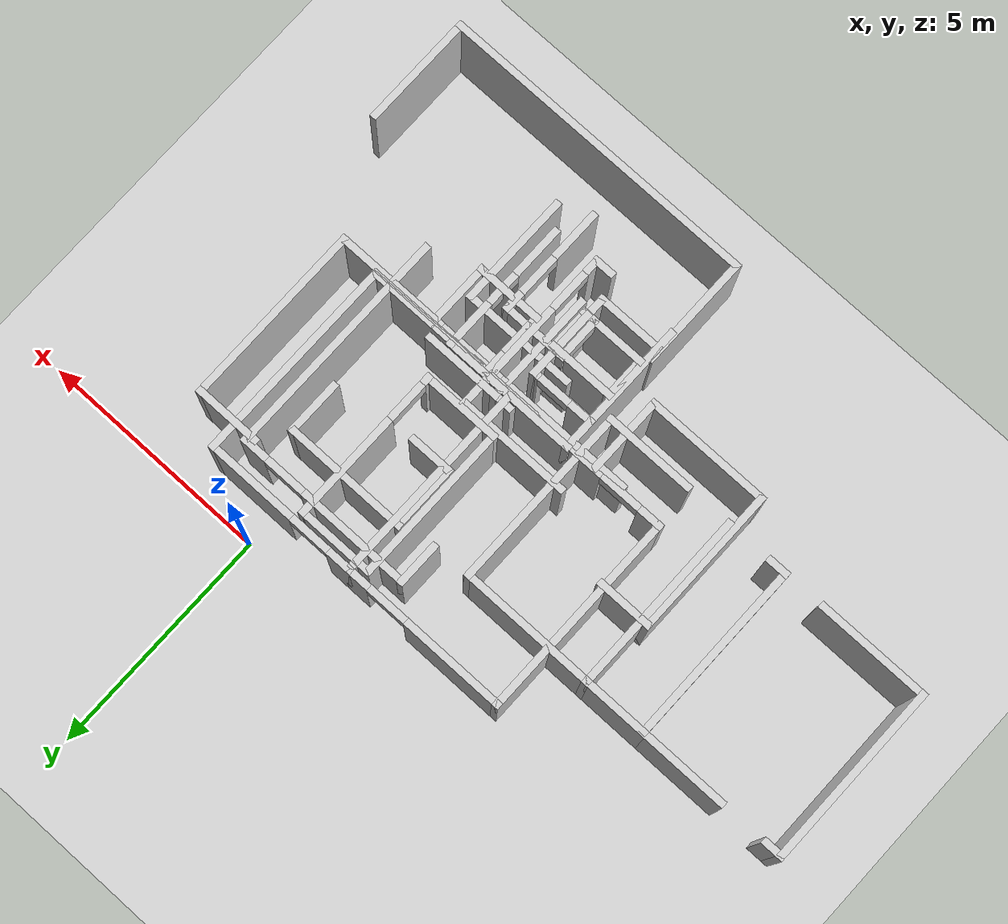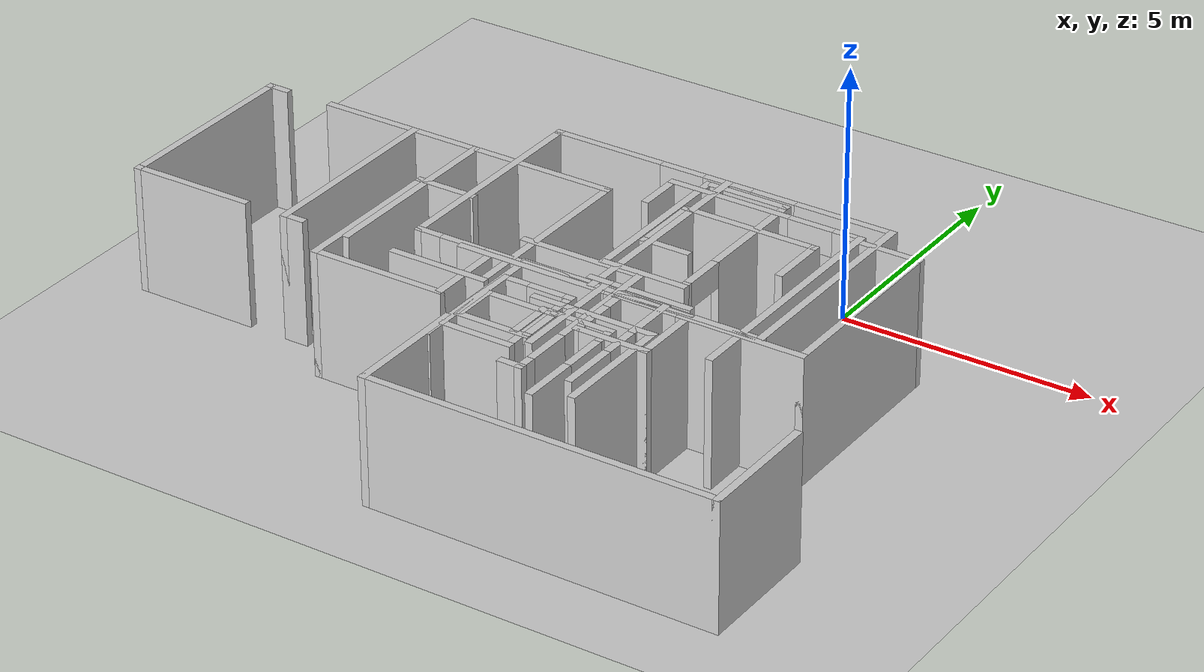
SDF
<sdf version='1.9'>
  <world name='default'>
    <plugin filename="gz-sim-physics-system" name="gz::sim::systems::Physics"/>
    <plugin filename="gz-sim-user-commands-system" name="gz::sim::systems::UserCommands"/>
    <plugin filename="gz-sim-scene-broadcaster-system" name="gz::sim::systems::SceneBroadcaster"/>
    <plugin filename="gz-sim-sensors-system" name="gz::sim::systems::Sensors">
      <render_engine>ogre2</render_engine>
    </plugin>
    <plugin filename="gz-sim-imu-system" name="gz::sim::systems::Imu"/>

    <light name='sun' type='directional'>
      <cast_shadows>true</cast_shadows>
      <pose>0 0 10 0 0 0</pose>
      <diffuse>0.800000012 0.800000012 0.800000012 1</diffuse>
      <specular>0.100000001 0.100000001 0.100000001 1</specular>
      <attenuation>
        <range>1000</range>
        <constant>0.90000000000000002</constant>
        <linear>0.01</linear>
        <quadratic>0.001</quadratic>
      </attenuation>
      <direction>-0.5 0.5 -1</direction>
      <spot>
        <inner_angle>0</inner_angle>
        <outer_angle>0</outer_angle>
        <falloff>0</falloff>
      </spot>
    </light>
    <model name='ground_plane'>
      <static>true</static>
      <link name='link'>
        <collision name='collision'>
          <geometry>
            <plane>
              <normal>0 0 1</normal>
              <size>100 100</size>
            </plane>
          </geometry>
          <surface>
            <friction>
              <ode>
                <mu>100</mu>
                <mu2>50</mu2>
              </ode>
              <torsional>
                <ode/>
              </torsional>
            </friction>
            <contact>
              <ode/>
            </contact>
            <bounce/>
          </surface>
        </collision>
        <visual name='visual'>
          <cast_shadows>false</cast_shadows>
          <geometry>
            <plane>
              <normal>0 0 1</normal>
              <size>100 100</size>
            </plane>
          </geometry>
          <material>
            <diffuse>0.8 0.8 0.8 1</diffuse>
          </material>
        </visual>
        <self_collide>false</self_collide>
        <kinematic>false</kinematic>
        <gravity>true</gravity>
      </link>
    </model>
    <gravity>0 0 -9.8000000000000007</gravity>
    <magnetic_field>6.0000000000000002e-06 2.3e-05 -4.1999999999999998e-05</magnetic_field>
    <atmosphere type='adiabatic'/>
    <physics name='default_physics' default='false' type='ode'>
      <max_step_size>0.001</max_step_size>
      <real_time_factor>1</real_time_factor>
      <real_time_update_rate>1000</real_time_update_rate>
    </physics>
    <scene>
      <ambient>0.4 0.4 0.4 1</ambient>
      <background>0.7 0.7 0.7 1</background>
      <shadows>true</shadows>
    </scene>
    <spherical_coordinates>
      <surface_model>EARTH_WGS84</surface_model>
      <latitude_deg>0</latitude_deg>
      <longitude_deg>0</longitude_deg>
      <elevation>0</elevation>
      <heading_deg>0</heading_deg>
    </spherical_coordinates>
    <model name='cma_escritorio'>
      <pose>-7.3949999999999996 -4.04 0 0 0 0</pose>
      <link name='Wall_11'>
        <collision name='Wall_11_Collision'>
          <geometry>
            <box>
              <size>2 0.14999999999999999 2.5</size>
            </box>
          </geometry>
          <pose>0 0 1.25 0 0 0</pose>
          <surface>
            <contact>
              <ode/>
            </contact>
            <bounce/>
            <friction>
              <torsional>
                <ode/>
              </torsional>
              <ode/>
            </friction>
          </surface>
        </collision>
        <visual name='Wall_11_Visual'>
          <pose>0 0 1.25 0 0 0</pose>
          <geometry>
            <box>
              <size>2 0.14999999999999999 2.5</size>
            </box>
          </geometry>
          <material>
            <diffuse>0.8 0.8 0.8 1</diffuse>
            <ambient>1 1 1 1</ambient>
          </material>
        </visual>
        <pose>-1.3999999999999999 1.9299999999999999 0 0 0 3.1415899999999999</pose>
        <self_collide>false</self_collide>
        <kinematic>false</kinematic>
        <gravity>true</gravity>
      </link>
      <link name='Wall_2'>
        <collision name='Wall_2_Collision'>
          <geometry>
            <box>
              <size>4 0.14999999999999999 2.5</size>
            </box>
          </geometry>
          <pose>0 0 1.25 0 0 0</pose>
          <surface>
            <contact>
              <ode/>
            </contact>
            <bounce/>
            <friction>
              <torsional>
                <ode/>
              </torsional>
              <ode/>
            </friction>
          </surface>
        </collision>
        <visual name='Wall_2_Visual'>
          <pose>0 0 1.25 0 0 0</pose>
          <geometry>
            <box>
              <size>4 0.14999999999999999 2.5</size>
            </box>
          </geometry>
          <material>
            <diffuse>0.8 0.8 0.8 1</diffuse>
            <ambient>1 1 1 1</ambient>
          </material>
        </visual>
        <pose>0.875 0.0050000000000000001 0 0 0 1.5708</pose>
        <self_collide>false</self_collide>
        <kinematic>false</kinematic>
        <gravity>true</gravity>
      </link>
      <link name='Wall_25'>
        <collision name='Wall_25_Collision'>
          <geometry>
            <box>
              <size>2.5 0.14999999999999999 2.5</size>
            </box>
          </geometry>
          <pose>0 0 1.25 0 0 0</pose>
          <surface>
            <contact>
              <ode/>
            </contact>
            <bounce/>
            <friction>
              <torsional>
                <ode/>
              </torsional>
              <ode/>
            </friction>
          </surface>
        </collision>
        <visual name='Wall_25_Visual'>
          <pose>0 0 1.25 0 0 0</pose>
          <geometry>
            <box>
              <size>2.5 0.14999999999999999 2.5</size>
            </box>
          </geometry>
          <material>
            <diffuse>0.8 0.8 0.8 1</diffuse>
            <ambient>1 1 1 1</ambient>
          </material>
        </visual>
        <pose>-2.5499999999999998 -1.9299999999999999 0 0 0 3.1415899999999999</pose>
        <self_collide>false</self_collide>
        <kinematic>false</kinematic>
        <gravity>true</gravity>
      </link>
      <link name='Wall_26'>
        <collision name='Wall_26_Collision'>
          <geometry>
            <box>
              <size>4 0.14999999999999999 2.5</size>
            </box>
          </geometry>
          <pose>0 0 1.25 0 0 0</pose>
          <surface>
            <contact>
              <ode/>
            </contact>
            <bounce/>
            <friction>
              <torsional>
                <ode/>
              </torsional>
              <ode/>
            </friction>
          </surface>
        </collision>
        <visual name='Wall_26_Visual'>
          <pose>0 0 1.25 0 0 0</pose>
          <geometry>
            <box>
              <size>4 0.14999999999999999 2.5</size>
            </box>
          </geometry>
          <material>
            <diffuse>0.8 0.8 0.8 1</diffuse>
            <ambient>1 1 1 1</ambient>
          </material>
        </visual>
        <pose>-3.7250000000000001 -0.0050000000000000001 0 0 0 1.5708</pose>
        <self_collide>false</self_collide>
        <kinematic>false</kinematic>
        <gravity>true</gravity>
      </link>
      <link name='Wall_27'>
        <collision name='Wall_27_Collision'>
          <geometry>
            <box>
              <size>0.5 0.14999999999999999 2.5</size>
            </box>
          </geometry>
          <pose>0 0 1.25 0 0 0</pose>
          <surface>
            <contact>
              <ode/>
            </contact>
            <bounce/>
            <friction>
              <torsional>
                <ode/>
              </torsional>
              <ode/>
            </friction>
          </surface>
        </collision>
        <visual name='Wall_27_Visual'>
          <pose>0 0 1.25 0 0 0</pose>
          <geometry>
            <box>
              <size>0.5 0.14999999999999999 2.5</size>
            </box>
          </geometry>
          <material>
            <diffuse>0.8 0.8 0.8 1</diffuse>
            <ambient>1 1 1 1</ambient>
          </material>
        </visual>
        <pose>-3.5499999999999998 1.9199999999999999 0 0 0 0</pose>
        <self_collide>false</self_collide>
        <kinematic>false</kinematic>
        <gravity>true</gravity>
      </link>
      <link name='Wall_3'>
        <collision name='Wall_3_Collision'>
          <geometry>
            <box>
              <size>3 0.14999999999999999 2.5</size>
            </box>
          </geometry>
          <pose>0 0 1.25 0 0 0</pose>
          <surface>
            <contact>
              <ode/>
            </contact>
            <bounce/>
            <friction>
              <torsional>
                <ode/>
              </torsional>
              <ode/>
            </friction>
          </surface>
        </collision>
        <visual name='Wall_3_Visual'>
          <pose>0 0 1.25 0 0 0</pose>
          <geometry>
            <box>
              <size>3 0.14999999999999999 2.5</size>
            </box>
          </geometry>
          <material>
            <diffuse>0.8 0.8 0.8 1</diffuse>
            <ambient>1 1 1 1</ambient>
          </material>
        </visual>
        <pose>2.2999999999999998 1.9299999999999999 0 0 0 0</pose>
        <self_collide>false</self_collide>
        <kinematic>false</kinematic>
        <gravity>true</gravity>
      </link>
      <link name='Wall_4'>
        <collision name='Wall_4_Collision'>
          <geometry>
            <box>
              <size>4 0.14999999999999999 2.5</size>
            </box>
          </geometry>
          <pose>0 0 1.25 0 0 0</pose>
          <surface>
            <contact>
              <ode/>
            </contact>
            <bounce/>
            <friction>
              <torsional>
                <ode/>
              </torsional>
              <ode/>
            </friction>
          </surface>
        </collision>
        <visual name='Wall_4_Visual'>
          <pose>0 0 1.25 0 0 0</pose>
          <geometry>
            <box>
              <size>4 0.14999999999999999 2.5</size>
            </box>
          </geometry>
          <material>
            <diffuse>0.8 0.8 0.8 1</diffuse>
            <ambient>1 1 1 1</ambient>
          </material>
        </visual>
        <pose>3.7250000000000001 0.0050000000000000001 0 0 0 -1.5708</pose>
        <self_collide>false</self_collide>
        <kinematic>false</kinematic>
        <gravity>true</gravity>
      </link>
      <link name='Wall_5'>
        <collision name='Wall_5_Collision'>
          <geometry>
            <box>
              <size>2 0.14999999999999999 2.5</size>
            </box>
          </geometry>
          <pose>0 0 1.25 0 0 0</pose>
          <surface>
            <contact>
              <ode/>
            </contact>
            <bounce/>
            <friction>
              <torsional>
                <ode/>
              </torsional>
              <ode/>
            </friction>
          </surface>
        </collision>
        <visual name='Wall_5_Visual'>
          <pose>0 0 1.25 0 0 0</pose>
          <geometry>
            <box>
              <size>2 0.14999999999999999 2.5</size>
            </box>
          </geometry>
          <material>
            <diffuse>0.8 0.8 0.8 1</diffuse>
            <ambient>1 1 1 1</ambient>
          </material>
        </visual>
        <pose>2.7999999999999998 -1.9199999999999999 0 0 0 3.1415899999999999</pose>
        <self_collide>false</self_collide>
        <kinematic>false</kinematic>
        <gravity>true</gravity>
      </link>
      <link name='Wall_7'>
        <collision name='Wall_7_Collision'>
          <geometry>
            <box>
              <size>1.5 0.14999999999999999 2.5</size>
            </box>
          </geometry>
          <pose>0 0 1.25 0 0 0</pose>
          <surface>
            <contact>
              <ode/>
            </contact>
            <bounce/>
            <friction>
              <torsional>
                <ode/>
              </torsional>
              <ode/>
            </friction>
          </surface>
        </collision>
        <visual name='Wall_7_Visual'>
          <pose>0 0 1.25 0 0 0</pose>
          <geometry>
            <box>
              <size>1.5 0.14999999999999999 2.5</size>
            </box>
          </geometry>
          <material>
            <diffuse>0.8 0.8 0.8 1</diffuse>
            <ambient>1 1 1 1</ambient>
          </material>
        </visual>
        <pose>0.20000000000000001 1.9299999999999999 0 0 0 3.1415899999999999</pose>
        <self_collide>false</self_collide>
        <kinematic>false</kinematic>
        <gravity>true</gravity>
      </link>
      <link name='Wall_8'>
        <collision name='Wall_8_Collision'>
          <geometry>
            <box>
              <size>4 0.14999999999999999 2.5</size>
            </box>
          </geometry>
          <pose>0 0 1.25 0 0 0</pose>
          <surface>
            <contact>
              <ode/>
            </contact>
            <bounce/>
            <friction>
              <torsional>
                <ode/>
              </torsional>
              <ode/>
            </friction>
          </surface>
        </collision>
        <visual name='Wall_8_Visual'>
          <pose>0 0 1.25 0 0 0</pose>
          <geometry>
            <box>
              <size>4 0.14999999999999999 2.5</size>
            </box>
          </geometry>
          <material>
            <diffuse>0.8 0.8 0.8 1</diffuse>
            <ambient>1 1 1 1</ambient>
          </material>
        </visual>
        <pose>-0.47499999999999998 0.0050000000000000001 0 0 0 -1.5708</pose>
        <self_collide>false</self_collide>
        <kinematic>false</kinematic>
        <gravity>true</gravity>
      </link>
      <link name='Wall_9'>
        <collision name='Wall_9_Collision'>
          <geometry>
            <box>
              <size>0.5 0.14999999999999999 2.5</size>
            </box>
          </geometry>
          <pose>0 0 1.25 0 0 0</pose>
          <surface>
            <contact>
              <ode/>
            </contact>
            <bounce/>
            <friction>
              <torsional>
                <ode/>
              </torsional>
              <ode/>
            </friction>
          </surface>
        </collision>
        <visual name='Wall_9_Visual'>
          <pose>0 0 1.25 0 0 0</pose>
          <geometry>
            <box>
              <size>0.5 0.14999999999999999 2.5</size>
            </box>
          </geometry>
          <material>
            <diffuse>0.8 0.8 0.8 1</diffuse>
            <ambient>1 1 1 1</ambient>
          </material>
        </visual>
        <pose>-0.29999999999999999 -1.9199999999999999 0 0 0 0</pose>
        <self_collide>false</self_collide>
        <kinematic>false</kinematic>
        <gravity>true</gravity>
      </link>
      <static>true</static>
    </model>
    <model name='cma_banheiro'>
      <pose>-0.81999999999999995 -2.5950000000000002 0 0 0 0</pose>
      <link name='Wall_0'>
        <collision name='Wall_0_Collision'>
          <geometry>
            <box>
              <size>1 0.14999999999999999 2.5</size>
            </box>
          </geometry>
          <pose>0 0 1.25 0 0 0</pose>
          <surface>
            <contact>
              <ode/>
            </contact>
            <bounce/>
            <friction>
              <torsional>
                <ode/>
              </torsional>
              <ode/>
            </friction>
          </surface>
        </collision>
        <visual name='Wall_0_Visual'>
          <pose>0 0 1.25 0 0 0</pose>
          <geometry>
            <box>
              <size>1 0.14999999999999999 2.5</size>
            </box>
          </geometry>
          <material>
            <diffuse>0.8 0.8 0.8 1</diffuse>
            <ambient>1 1 1 1</ambient>
          </material>
        </visual>
        <pose>-0.875 -0.67500000000000004 0 0 0 3.1415899999999999</pose>
        <self_collide>false</self_collide>
        <kinematic>false</kinematic>
        <gravity>true</gravity>
      </link>
      <link name='Wall_1'>
        <collision name='Wall_1_Collision'>
          <geometry>
            <box>
              <size>1.5 0.14999999999999999 2.5</size>
            </box>
          </geometry>
          <pose>0 0 1.25 0 0 0</pose>
          <surface>
            <contact>
              <ode/>
            </contact>
            <bounce/>
            <friction>
              <torsional>
                <ode/>
              </torsional>
              <ode/>
            </friction>
          </surface>
        </collision>
        <visual name='Wall_1_Visual'>
          <pose>0 0 1.25 0 0 0</pose>
          <geometry>
            <box>
              <size>1.5 0.14999999999999999 2.5</size>
            </box>
          </geometry>
          <material>
            <diffuse>0.8 0.8 0.8 1</diffuse>
            <ambient>1 1 1 1</ambient>
          </material>
        </visual>
        <pose>-1.3 0 0 0 0 1.5708</pose>
        <self_collide>false</self_collide>
        <kinematic>false</kinematic>
        <gravity>true</gravity>
      </link>
      <link name='Wall_2'>
        <collision name='Wall_2_Collision'>
          <geometry>
            <box>
              <size>2.75 0.14999999999999999 2.5</size>
            </box>
          </geometry>
          <pose>0 0 1.25 0 0 0</pose>
          <surface>
            <contact>
              <ode/>
            </contact>
            <bounce/>
            <friction>
              <torsional>
                <ode/>
              </torsional>
              <ode/>
            </friction>
          </surface>
        </collision>
        <visual name='Wall_2_Visual'>
          <pose>0 0 1.25 0 0 0</pose>
          <geometry>
            <box>
              <size>2.75 0.14999999999999999 2.5</size>
            </box>
          </geometry>
          <material>
            <diffuse>0.8 0.8 0.8 1</diffuse>
            <ambient>1 1 1 1</ambient>
          </material>
        </visual>
        <pose>0 0.67500000000000004 0 0 0 0</pose>
        <self_collide>false</self_collide>
        <kinematic>false</kinematic>
        <gravity>true</gravity>
      </link>
      <link name='Wall_4'>
        <collision name='Wall_4_Collision'>
          <geometry>
            <box>
              <size>1.25 0.14999999999999999 2.5</size>
            </box>
          </geometry>
          <pose>0 0 1.25 0 0 0</pose>
          <surface>
            <contact>
              <ode/>
            </contact>
            <bounce/>
            <friction>
              <torsional>
                <ode/>
              </torsional>
              <ode/>
            </friction>
          </surface>
        </collision>
        <visual name='Wall_4_Visual'>
          <pose>0 0 1.25 0 0 0</pose>
          <geometry>
            <box>
              <size>1.25 0.14999999999999999 2.5</size>
            </box>
          </geometry>
          <material>
            <diffuse>0.8 0.8 0.8 1</diffuse>
            <ambient>1 1 1 1</ambient>
          </material>
        </visual>
        <pose>1.3 0.125 0 0 0 -1.5708</pose>
        <self_collide>false</self_collide>
        <kinematic>false</kinematic>
        <gravity>true</gravity>
      </link>
      <static>true</static>
    </model>
    <model name='cma_varanda1'>
      <pose>-1.49 -2.6150000000000002 0 0 0 0</pose>
      <link name='Wall_0'>
        <pose>0.80000000000000004 0 0 0 0 -1.5708</pose>
        <visual name='Wall_0_Visual_0'>
          <pose>-0.55249999999999999 0 1.25 0 0 0</pose>
          <geometry>
            <box>
              <size>2.395 0.14999999999999999 2.5</size>
            </box>
          </geometry>
          <material>
            <diffuse>0.8 0.8 0.8 1</diffuse>
            <ambient>1 1 1 1</ambient>
          </material>
        </visual>
        <collision name='Wall_0_Collision_0'>
          <geometry>
            <box>
              <size>2.395 0.14999999999999999 2.5</size>
            </box>
          </geometry>
          <pose>-0.55249999999999999 0 1.25 0 0 0</pose>
          <surface>
            <contact>
              <ode/>
            </contact>
            <bounce/>
            <friction>
              <torsional>
                <ode/>
              </torsional>
              <ode/>
            </friction>
          </surface>
        </collision>
        <visual name='Wall_0_Visual_1'>
          <pose>1.6375 0 1.25 0 0 0</pose>
          <geometry>
            <box>
              <size>0.22500000000000001 0.14999999999999999 2.5</size>
            </box>
          </geometry>
          <material>
            <diffuse>0.8 0.8 0.8 1</diffuse>
            <ambient>1 1 1 1</ambient>
          </material>
        </visual>
        <collision name='Wall_0_Collision_1'>
          <geometry>
            <box>
              <size>0.22500000000000001 0.14999999999999999 2.5</size>
            </box>
          </geometry>
          <pose>1.6375 0 1.25 0 0 0</pose>
          <surface>
            <contact>
              <ode/>
            </contact>
            <bounce/>
            <friction>
              <torsional>
                <ode/>
              </torsional>
              <ode/>
            </friction>
          </surface>
        </collision>
        <visual name='Wall_0_Visual_2'>
          <pose>1.085 0 2.25 0 0 0</pose>
          <geometry>
            <box>
              <size>0.88 0.14999999999999999 0.5</size>
            </box>
          </geometry>
          <material>
            <diffuse>0.8 0.8 0.8 1</diffuse>
            <ambient>1 1 1 1</ambient>
          </material>
        </visual>
        <collision name='Wall_0_Collision_2'>
          <geometry>
            <box>
              <size>0.88 0.14999999999999999 0.5</size>
            </box>
          </geometry>
          <pose>1.085 0 2.25 0 0 0</pose>
          <surface>
            <contact>
              <ode/>
            </contact>
            <bounce/>
            <friction>
              <torsional>
                <ode/>
              </torsional>
              <ode/>
            </friction>
          </surface>
        </collision>
        <self_collide>false</self_collide>
        <kinematic>false</kinematic>
        <gravity>true</gravity>
      </link>
      <link name='Wall_1'>
        <collision name='Wall_1_Collision'>
          <geometry>
            <box>
              <size>1.75 0.14999999999999999 2.5</size>
            </box>
          </geometry>
          <pose>0 0 1.25 0 0 0</pose>
          <surface>
            <contact>
              <ode/>
            </contact>
            <bounce/>
            <friction>
              <torsional>
                <ode/>
              </torsional>
              <ode/>
            </friction>
          </surface>
        </collision>
        <visual name='Wall_1_Visual'>
          <pose>0 0 1.25 0 0 0</pose>
          <geometry>
            <box>
              <size>1.75 0.14999999999999999 2.5</size>
            </box>
          </geometry>
          <material>
            <diffuse>0.8 0.8 0.8 1</diffuse>
            <ambient>1 1 1 1</ambient>
          </material>
        </visual>
        <pose>0 -1.675 0 0 0 3.1415899999999999</pose>
        <self_collide>false</self_collide>
        <kinematic>false</kinematic>
        <gravity>true</gravity>
      </link>
      <link name='Wall_2'>
        <collision name='Wall_2_Collision'>
          <geometry>
            <box>
              <size>3.5 0.14999999999999999 2.5</size>
            </box>
          </geometry>
          <pose>0 0 1.25 0 0 0</pose>
          <surface>
            <contact>
              <ode/>
            </contact>
            <bounce/>
            <friction>
              <torsional>
                <ode/>
              </torsional>
              <ode/>
            </friction>
          </surface>
        </collision>
        <visual name='Wall_2_Visual'>
          <pose>0 0 1.25 0 0 0</pose>
          <geometry>
            <box>
              <size>3.5 0.14999999999999999 2.5</size>
            </box>
          </geometry>
          <material>
            <diffuse>0.8 0.8 0.8 1</diffuse>
            <ambient>1 1 1 1</ambient>
          </material>
        </visual>
        <pose>-0.80000000000000004 0 0 0 0 1.5708</pose>
        <self_collide>false</self_collide>
        <kinematic>false</kinematic>
        <gravity>true</gravity>
      </link>
      <link name='Wall_3'>
        <collision name='Wall_3_Collision'>
          <geometry>
            <box>
              <size>1.75 0.14999999999999999 2.5</size>
            </box>
          </geometry>
          <pose>0 0 1.25 0 0 0</pose>
          <surface>
            <contact>
              <ode/>
            </contact>
            <bounce/>
            <friction>
              <torsional>
                <ode/>
              </torsional>
              <ode/>
            </friction>
          </surface>
        </collision>
        <visual name='Wall_3_Visual'>
          <pose>0 0 1.25 0 0 0</pose>
          <geometry>
            <box>
              <size>1.75 0.14999999999999999 2.5</size>
            </box>
          </geometry>
          <material>
            <diffuse>0.8 0.8 0.8 1</diffuse>
            <ambient>1 1 1 1</ambient>
          </material>
        </visual>
        <pose>0 1.675 0 0 0 0</pose>
        <self_collide>false</self_collide>
        <kinematic>false</kinematic>
        <gravity>true</gravity>
      </link>
      <static>true</static>
    </model>
    <model name='cma_quartos'>
      <pose>-2.6549999999999998 -3.7149999999999999 0 0 0 0</pose>
      <link name='Wall_0'>
        <collision name='Wall_0_Collision'>
          <geometry>
            <box>
              <size>4.5 0.14999999999999999 2.5</size>
            </box>
          </geometry>
          <pose>0 0 1.25 0 0 0</pose>
          <surface>
            <contact>
              <ode/>
            </contact>
            <bounce/>
            <friction>
              <torsional>
                <ode/>
              </torsional>
              <ode/>
            </friction>
          </surface>
        </collision>
        <visual name='Wall_0_Visual'>
          <pose>0 0 1.25 0 0 0</pose>
          <geometry>
            <box>
              <size>4.5 0.14999999999999999 2.5</size>
            </box>
          </geometry>
          <material>
            <diffuse>0.8 0.8 0.8 1</diffuse>
            <ambient>1 1 1 1</ambient>
          </material>
        </visual>
        <pose>0.64500000000000002 0.81000000000000005 0 0 0 -1.5708</pose>
        <self_collide>false</self_collide>
        <kinematic>false</kinematic>
        <gravity>true</gravity>
      </link>
      <link name='Wall_1'>
        <pose>-1.155 -1.365 0 0 0 3.1415899999999999</pose>
        <visual name='Wall_1_Visual_0'>
          <pose>-0.72250000000000003 0 1.25 0 0 0</pose>
          <geometry>
            <box>
              <size>2.3050000000000002 0.14999999999999999 2.5</size>
            </box>
          </geometry>
          <material>
            <diffuse>0.8 0.8 0.8 1</diffuse>
            <ambient>1 1 1 1</ambient>
          </material>
        </visual>
        <collision name='Wall_1_Collision_0'>
          <geometry>
            <box>
              <size>2.3050000000000002 0.14999999999999999 2.5</size>
            </box>
          </geometry>
          <pose>-0.72250000000000003 0 1.25 0 0 0</pose>
          <surface>
            <contact>
              <ode/>
            </contact>
            <bounce/>
            <friction>
              <torsional>
                <ode/>
              </torsional>
              <ode/>
            </friction>
          </surface>
        </collision>
        <visual name='Wall_1_Visual_1'>
          <pose>1.6025 0 1.25 0 0 0</pose>
          <geometry>
            <box>
              <size>0.54500000000000004 0.14999999999999999 2.5</size>
            </box>
          </geometry>
          <material>
            <diffuse>0.8 0.8 0.8 1</diffuse>
            <ambient>1 1 1 1</ambient>
          </material>
        </visual>
        <collision name='Wall_1_Collision_1'>
          <geometry>
            <box>
              <size>0.54500000000000004 0.14999999999999999 2.5</size>
            </box>
          </geometry>
          <pose>1.6025 0 1.25 0 0 0</pose>
          <surface>
            <contact>
              <ode/>
            </contact>
            <bounce/>
            <friction>
              <torsional>
                <ode/>
              </torsional>
              <ode/>
            </friction>
          </surface>
        </collision>
        <visual name='Wall_1_Visual_2'>
          <pose>0.88 0 2.25 0 0 0</pose>
          <geometry>
            <box>
              <size>0.90000000000000002 0.14999999999999999 0.5</size>
            </box>
          </geometry>
          <material>
            <diffuse>0.8 0.8 0.8 1</diffuse>
            <ambient>1 1 1 1</ambient>
          </material>
        </visual>
        <collision name='Wall_1_Collision_2'>
          <geometry>
            <box>
              <size>0.90000000000000002 0.14999999999999999 0.5</size>
            </box>
          </geometry>
          <pose>0.88 0 2.25 0 0 0</pose>
          <surface>
            <contact>
              <ode/>
            </contact>
            <bounce/>
            <friction>
              <torsional>
                <ode/>
              </torsional>
              <ode/>
            </friction>
          </surface>
        </collision>
        <self_collide>false</self_collide>
        <kinematic>false</kinematic>
        <gravity>true</gravity>
      </link>
      <link name='Wall_10'>
        <collision name='Wall_10_Collision'>
          <geometry>
            <box>
              <size>1.75 0.14999999999999999 2.5</size>
            </box>
          </geometry>
          <pose>0 0 1.25 0 0 0</pose>
          <surface>
            <contact>
              <ode/>
            </contact>
            <bounce/>
            <friction>
              <torsional>
                <ode/>
              </torsional>
              <ode/>
            </friction>
          </surface>
        </collision>
        <visual name='Wall_10_Visual'>
          <pose>0 0 1.25 0 0 0</pose>
          <geometry>
            <box>
              <size>1.75 0.14999999999999999 2.5</size>
            </box>
          </geometry>
          <material>
            <diffuse>0.8 0.8 0.8 1</diffuse>
            <ambient>1 1 1 1</ambient>
          </material>
        </visual>
        <pose>-1.395 -2.1850000000000001 0 0 0 -1.5708</pose>
        <self_collide>false</self_collide>
        <kinematic>false</kinematic>
        <gravity>true</gravity>
      </link>
      <link name='Wall_11'>
        <collision name='Wall_11_Collision'>
          <geometry>
            <box>
              <size>2.75 0.14999999999999999 2.5</size>
            </box>
          </geometry>
          <pose>0 0 1.25 0 0 0</pose>
          <surface>
            <contact>
              <ode/>
            </contact>
            <bounce/>
            <friction>
              <torsional>
                <ode/>
              </torsional>
              <ode/>
            </friction>
          </surface>
        </collision>
        <visual name='Wall_11_Visual'>
          <pose>0 0 1.25 0 0 0</pose>
          <geometry>
            <box>
              <size>2.75 0.14999999999999999 2.5</size>
            </box>
          </geometry>
          <material>
            <diffuse>0.8 0.8 0.8 1</diffuse>
            <ambient>1 1 1 1</ambient>
          </material>
        </visual>
        <pose>-2.6949999999999998 -2.9849999999999999 0 0 0 3.1415899999999999</pose>
        <self_collide>false</self_collide>
        <kinematic>false</kinematic>
        <gravity>true</gravity>
      </link>
      <link name='Wall_12'>
        <collision name='Wall_12_Collision'>
          <geometry>
            <box>
              <size>3.25 0.14999999999999999 2.5</size>
            </box>
          </geometry>
          <pose>0 0 1.25 0 0 0</pose>
          <surface>
            <contact>
              <ode/>
            </contact>
            <bounce/>
            <friction>
              <torsional>
                <ode/>
              </torsional>
              <ode/>
            </friction>
          </surface>
        </collision>
        <visual name='Wall_12_Visual'>
          <pose>0 0 1.25 0 0 0</pose>
          <geometry>
            <box>
              <size>3.25 0.14999999999999999 2.5</size>
            </box>
          </geometry>
          <material>
            <diffuse>0.8 0.8 0.8 1</diffuse>
            <ambient>1 1 1 1</ambient>
          </material>
        </visual>
        <pose>-3.9950000000000001 -1.4350000000000001 0 0 0 1.5708</pose>
        <self_collide>false</self_collide>
        <kinematic>false</kinematic>
        <gravity>true</gravity>
      </link>
      <link name='Wall_13'>
        <collision name='Wall_13_Collision'>
          <geometry>
            <box>
              <size>1.25 0.14999999999999999 2.5</size>
            </box>
          </geometry>
          <pose>0 0 1.25 0 0 0</pose>
          <surface>
            <contact>
              <ode/>
            </contact>
            <bounce/>
            <friction>
              <torsional>
                <ode/>
              </torsional>
              <ode/>
            </friction>
          </surface>
        </collision>
        <visual name='Wall_13_Visual'>
          <pose>0 0 1.25 0 0 0</pose>
          <geometry>
            <box>
              <size>1.25 0.14999999999999999 2.5</size>
            </box>
          </geometry>
          <material>
            <diffuse>0.8 0.8 0.8 1</diffuse>
            <ambient>1 1 1 1</ambient>
          </material>
        </visual>
        <pose>-3.4449999999999998 0.115 0 0 0 0</pose>
        <self_collide>false</self_collide>
        <kinematic>false</kinematic>
        <gravity>true</gravity>
      </link>
      <link name='Wall_2'>
        <collision name='Wall_2_Collision'>
          <geometry>
            <box>
              <size>4.5 0.14999999999999999 2.5</size>
            </box>
          </geometry>
          <pose>0 0 1.25 0 0 0</pose>
          <surface>
            <contact>
              <ode/>
            </contact>
            <bounce/>
            <friction>
              <torsional>
                <ode/>
              </torsional>
              <ode/>
            </friction>
          </surface>
        </collision>
        <visual name='Wall_2_Visual'>
          <pose>0 0 1.25 0 0 0</pose>
          <geometry>
            <box>
              <size>4.5 0.14999999999999999 2.5</size>
            </box>
          </geometry>
          <material>
            <diffuse>0.8 0.8 0.8 1</diffuse>
            <ambient>1 1 1 1</ambient>
          </material>
        </visual>
        <pose>-2.9550000000000001 0.81000000000000005 0 0 0 1.5708</pose>
        <self_collide>false</self_collide>
        <kinematic>false</kinematic>
        <gravity>true</gravity>
      </link>
      <link name='Wall_3'>
        <pose>-1.155 2.9849999999999999 0 0 0 0</pose>
        <visual name='Wall_3_Visual_0'>
          <pose>-0.73250000000000004 0 1.25 0 0 0</pose>
          <geometry>
            <box>
              <size>2.2850000000000001 0.14999999999999999 2.5</size>
            </box>
          </geometry>
          <material>
            <diffuse>0.8 0.8 0.8 1</diffuse>
            <ambient>1 1 1 1</ambient>
          </material>
        </visual>
        <collision name='Wall_3_Collision_0'>
          <geometry>
            <box>
              <size>2.2850000000000001 0.14999999999999999 2.5</size>
            </box>
          </geometry>
          <pose>-0.73250000000000004 0 1.25 0 0 0</pose>
          <surface>
            <contact>
              <ode/>
            </contact>
            <bounce/>
            <friction>
              <torsional>
                <ode/>
              </torsional>
              <ode/>
            </friction>
          </surface>
        </collision>
        <visual name='Wall_3_Visual_1'>
          <pose>1.5925 0 1.25 0 0 0</pose>
          <geometry>
            <box>
              <size>0.56499999999999995 0.14999999999999999 2.5</size>
            </box>
          </geometry>
          <material>
            <diffuse>0.8 0.8 0.8 1</diffuse>
            <ambient>1 1 1 1</ambient>
          </material>
        </visual>
        <collision name='Wall_3_Collision_1'>
          <geometry>
            <box>
              <size>0.56499999999999995 0.14999999999999999 2.5</size>
            </box>
          </geometry>
          <pose>1.5925 0 1.25 0 0 0</pose>
          <surface>
            <contact>
              <ode/>
            </contact>
            <bounce/>
            <friction>
              <torsional>
                <ode/>
              </torsional>
              <ode/>
            </friction>
          </surface>
        </collision>
        <visual name='Wall_3_Visual_2'>
          <pose>0.85999999999999999 0 2.25 0 0 0</pose>
          <geometry>
            <box>
              <size>0.90000000000000002 0.14999999999999999 0.5</size>
            </box>
          </geometry>
          <material>
            <diffuse>0.8 0.8 0.8 1</diffuse>
            <ambient>1 1 1 1</ambient>
          </material>
        </visual>
        <collision name='Wall_3_Collision_2'>
          <geometry>
            <box>
              <size>0.90000000000000002 0.14999999999999999 0.5</size>
            </box>
          </geometry>
          <pose>0.85999999999999999 0 2.25 0 0 0</pose>
          <surface>
            <contact>
              <ode/>
            </contact>
            <bounce/>
            <friction>
              <torsional>
                <ode/>
              </torsional>
              <ode/>
            </friction>
          </surface>
        </collision>
        <self_collide>false</self_collide>
        <kinematic>false</kinematic>
        <gravity>true</gravity>
      </link>
      <link name='Wall_6'>
        <pose>2.3199999999999998 2.9849999999999999 0 0 0 0</pose>
        <visual name='Wall_6_Visual_0'>
          <pose>-1.4575 0 1.25 0 0 0</pose>
          <geometry>
            <box>
              <size>0.58499999999999996 0.14999999999999999 2.5</size>
            </box>
          </geometry>
          <material>
            <diffuse>0.8 0.8 0.8 1</diffuse>
            <ambient>1 1 1 1</ambient>
          </material>
        </visual>
        <collision name='Wall_6_Collision_0'>
          <geometry>
            <box>
              <size>0.58499999999999996 0.14999999999999999 2.5</size>
            </box>
          </geometry>
          <pose>-1.4575 0 1.25 0 0 0</pose>
          <surface>
            <contact>
              <ode/>
            </contact>
            <bounce/>
            <friction>
              <torsional>
                <ode/>
              </torsional>
              <ode/>
            </friction>
          </surface>
        </collision>
        <visual name='Wall_6_Visual_1'>
          <pose>0.74250000000000005 0 1.25 0 0 0</pose>
          <geometry>
            <box>
              <size>2.0150000000000001 0.14999999999999999 2.5</size>
            </box>
          </geometry>
          <material>
            <diffuse>0.8 0.8 0.8 1</diffuse>
            <ambient>1 1 1 1</ambient>
          </material>
        </visual>
        <collision name='Wall_6_Collision_1'>
          <geometry>
            <box>
              <size>2.0150000000000001 0.14999999999999999 2.5</size>
            </box>
          </geometry>
          <pose>0.74250000000000005 0 1.25 0 0 0</pose>
          <surface>
            <contact>
              <ode/>
            </contact>
            <bounce/>
            <friction>
              <torsional>
                <ode/>
              </torsional>
              <ode/>
            </friction>
          </surface>
        </collision>
        <visual name='Wall_6_Visual_2'>
          <pose>-0.71499999999999997 0 2.25 0 0 0</pose>
          <geometry>
            <box>
              <size>0.90000000000000002 0.14999999999999999 0.5</size>
            </box>
          </geometry>
          <material>
            <diffuse>0.8 0.8 0.8 1</diffuse>
            <ambient>1 1 1 1</ambient>
          </material>
        </visual>
        <collision name='Wall_6_Collision_2'>
          <geometry>
            <box>
              <size>0.90000000000000002 0.14999999999999999 0.5</size>
            </box>
          </geometry>
          <pose>-0.71499999999999997 0 2.25 0 0 0</pose>
          <surface>
            <contact>
              <ode/>
            </contact>
            <bounce/>
            <friction>
              <torsional>
                <ode/>
              </torsional>
              <ode/>
            </friction>
          </surface>
        </collision>
        <self_collide>false</self_collide>
        <kinematic>false</kinematic>
        <gravity>true</gravity>
      </link>
      <link name='Wall_7'>
        <collision name='Wall_7_Collision'>
          <geometry>
            <box>
              <size>4.5 0.14999999999999999 2.5</size>
            </box>
          </geometry>
          <pose>0 0 1.25 0 0 0</pose>
          <surface>
            <contact>
              <ode/>
            </contact>
            <bounce/>
            <friction>
              <torsional>
                <ode/>
              </torsional>
              <ode/>
            </friction>
          </surface>
        </collision>
        <visual name='Wall_7_Visual'>
          <pose>0 0 1.25 0 0 0</pose>
          <geometry>
            <box>
              <size>4.5 0.14999999999999999 2.5</size>
            </box>
          </geometry>
          <material>
            <diffuse>0.8 0.8 0.8 1</diffuse>
            <ambient>1 1 1 1</ambient>
          </material>
        </visual>
        <pose>3.9950000000000001 0.81000000000000005 0 0 0 -1.5708</pose>
        <self_collide>false</self_collide>
        <kinematic>false</kinematic>
        <gravity>true</gravity>
      </link>
      <link name='Wall_8'>
        <collision name='Wall_8_Collision'>
          <geometry>
            <box>
              <size>3.5 0.14999999999999999 2.5</size>
            </box>
          </geometry>
          <pose>0 0 1.25 0 0 0</pose>
          <surface>
            <contact>
              <ode/>
            </contact>
            <bounce/>
            <friction>
              <torsional>
                <ode/>
              </torsional>
              <ode/>
            </friction>
          </surface>
        </collision>
        <visual name='Wall_8_Visual'>
          <pose>0 0 1.25 0 0 0</pose>
          <geometry>
            <box>
              <size>3.5 0.14999999999999999 2.5</size>
            </box>
          </geometry>
          <material>
            <diffuse>0.8 0.8 0.8 1</diffuse>
            <ambient>1 1 1 1</ambient>
          </material>
        </visual>
        <pose>2.3199999999999998 -1.365 0 0 0 3.1415899999999999</pose>
        <self_collide>false</self_collide>
        <kinematic>false</kinematic>
        <gravity>true</gravity>
      </link>
      <static>true</static>
    </model>
    <model name='cma_parede_t'>
      <pose>-1.1850000000000001 -6.0449999999999999 0 0 0 0</pose>
      <link name='Wall_15'>
        <collision name='Wall_15_Collision'>
          <geometry>
            <box>
              <size>2.5 0.14999999999999999 2.5</size>
            </box>
          </geometry>
          <pose>0 0 1.25 0 0 0</pose>
          <surface>
            <contact>
              <ode/>
            </contact>
            <bounce/>
            <friction>
              <torsional>
                <ode/>
              </torsional>
              <ode/>
            </friction>
          </surface>
        </collision>
        <visual name='Wall_15_Visual'>
          <pose>0 0 1.25 0 0 0</pose>
          <geometry>
            <box>
              <size>2.5 0.14999999999999999 2.5</size>
            </box>
          </geometry>
          <material>
            <diffuse>0.8 0.8 0.8 1</diffuse>
            <ambient>1 1 1 1</ambient>
          </material>
        </visual>
        <pose>-0.625 0 0 0 0 1.5708</pose>
        <self_collide>false</self_collide>
        <kinematic>false</kinematic>
        <gravity>true</gravity>
      </link>
      <link name='Wall_16'>
        <collision name='Wall_16_Collision'>
          <geometry>
            <box>
              <size>0.5 0.14999999999999999 2.5</size>
            </box>
          </geometry>
          <pose>0 0 1.25 0 0 0</pose>
          <surface>
            <contact>
              <ode/>
            </contact>
            <bounce/>
            <friction>
              <torsional>
                <ode/>
              </torsional>
              <ode/>
            </friction>
          </surface>
        </collision>
        <visual name='Wall_16_Visual'>
          <pose>0 0 1.25 0 0 0</pose>
          <geometry>
            <box>
              <size>0.5 0.14999999999999999 2.5</size>
            </box>
          </geometry>
          <material>
            <diffuse>0.8 0.8 0.8 1</diffuse>
            <ambient>1 1 1 1</ambient>
          </material>
        </visual>
        <pose>-0.80000000000000004 1.175 0 0 0 3.1415899999999999</pose>
        <self_collide>false</self_collide>
        <kinematic>false</kinematic>
        <gravity>true</gravity>
      </link>
      <link name='Wall_18'>
        <collision name='Wall_18_Collision'>
          <geometry>
            <box>
              <size>1.75 0.14999999999999999 2.5</size>
            </box>
          </geometry>
          <pose>0 0 1.25 0 0 0</pose>
          <surface>
            <contact>
              <ode/>
            </contact>
            <bounce/>
            <friction>
              <torsional>
                <ode/>
              </torsional>
              <ode/>
            </friction>
          </surface>
        </collision>
        <visual name='Wall_18_Visual'>
          <pose>0 0 1.25 0 0 0</pose>
          <geometry>
            <box>
              <size>1.75 0.14999999999999999 2.5</size>
            </box>
          </geometry>
          <material>
            <diffuse>0.8 0.8 0.8 1</diffuse>
            <ambient>1 1 1 1</ambient>
          </material>
        </visual>
        <pose>0.17499999999999999 1.175 0 0 0 0</pose>
        <self_collide>false</self_collide>
        <kinematic>false</kinematic>
        <gravity>true</gravity>
      </link>
      <static>true</static>
    </model>
    <model name='cma_parede_L'>
      <pose>-1.2150000000000001 -3.2450000000000001 0 0 0 0</pose>
      <link name='Wall_0'>
        <pose>0 -1.925 0 0 0 0</pose>
        <visual name='Wall_0_Visual_0'>
          <pose>-1.9850000000000001 0 1.25 0 0 0</pose>
          <geometry>
            <box>
              <size>3.0299999999999998 0.14999999999999999 2.5</size>
            </box>
          </geometry>
          <material>
            <diffuse>0.8 0.8 0.8 1</diffuse>
            <ambient>1 1 1 1</ambient>
          </material>
        </visual>
        <collision name='Wall_0_Collision_0'>
          <geometry>
            <box>
              <size>3.0299999999999998 0.14999999999999999 2.5</size>
            </box>
          </geometry>
          <pose>-1.9850000000000001 0 1.25 0 0 0</pose>
          <surface>
            <contact>
              <ode/>
            </contact>
            <bounce/>
            <friction>
              <torsional>
                <ode/>
              </torsional>
              <ode/>
            </friction>
          </surface>
        </collision>
        <visual name='Wall_0_Visual_1'>
          <pose>2.2400000000000002 0 1.25 0 0 0</pose>
          <geometry>
            <box>
              <size>2.52 0.14999999999999999 2.5</size>
            </box>
          </geometry>
          <material>
            <diffuse>0.8 0.8 0.8 1</diffuse>
            <ambient>1 1 1 1</ambient>
          </material>
        </visual>
        <collision name='Wall_0_Collision_1'>
          <geometry>
            <box>
              <size>2.52 0.14999999999999999 2.5</size>
            </box>
          </geometry>
          <pose>2.2400000000000002 0 1.25 0 0 0</pose>
          <surface>
            <contact>
              <ode/>
            </contact>
            <bounce/>
            <friction>
              <torsional>
                <ode/>
              </torsional>
              <ode/>
            </friction>
          </surface>
        </collision>
        <visual name='Wall_0_Visual_2'>
          <pose>0.255 0 2.25 0 0 0</pose>
          <geometry>
            <box>
              <size>1.45 0.14999999999999999 0.5</size>
            </box>
          </geometry>
          <material>
            <diffuse>0.8 0.8 0.8 1</diffuse>
            <ambient>1 1 1 1</ambient>
          </material>
        </visual>
        <collision name='Wall_0_Collision_2'>
          <geometry>
            <box>
              <size>1.45 0.14999999999999999 0.5</size>
            </box>
          </geometry>
          <pose>0.255 0 2.25 0 0 0</pose>
          <surface>
            <contact>
              <ode/>
            </contact>
            <bounce/>
            <friction>
              <torsional>
                <ode/>
              </torsional>
              <ode/>
            </friction>
          </surface>
        </collision>
        <self_collide>false</self_collide>
        <kinematic>false</kinematic>
        <gravity>true</gravity>
      </link>
      <link name='Wall_1'>
        <collision name='Wall_1_Collision'>
          <geometry>
            <box>
              <size>4 0.14999999999999999 2.5</size>
            </box>
          </geometry>
          <pose>0 0 1.25 0 0 0</pose>
          <surface>
            <contact>
              <ode/>
            </contact>
            <bounce/>
            <friction>
              <torsional>
                <ode/>
              </torsional>
              <ode/>
            </friction>
          </surface>
        </collision>
        <visual name='Wall_1_Visual'>
          <pose>0 0 1.25 0 0 0</pose>
          <geometry>
            <box>
              <size>4 0.14999999999999999 2.5</size>
            </box>
          </geometry>
          <material>
            <diffuse>0.8 0.8 0.8 1</diffuse>
            <ambient>1 1 1 1</ambient>
          </material>
        </visual>
        <pose>3.4249999999999998 0 0 0 0 1.5708</pose>
        <self_collide>false</self_collide>
        <kinematic>false</kinematic>
        <gravity>true</gravity>
      </link>
      <link name='Wall_2'>
        <collision name='Wall_2_Collision'>
          <geometry>
            <box>
              <size>1.5 0.14999999999999999 2.5</size>
            </box>
          </geometry>
          <pose>0 0 1.25 0 0 0</pose>
          <surface>
            <contact>
              <ode/>
            </contact>
            <bounce/>
            <friction>
              <torsional>
                <ode/>
              </torsional>
              <ode/>
            </friction>
          </surface>
        </collision>
        <visual name='Wall_2_Visual'>
          <pose>0 0 1.25 0 0 0</pose>
          <geometry>
            <box>
              <size>1.5 0.14999999999999999 2.5</size>
            </box>
          </geometry>
          <material>
            <diffuse>0.8 0.8 0.8 1</diffuse>
            <ambient>1 1 1 1</ambient>
          </material>
        </visual>
        <pose>2.75 1.925 0 0 0 3.1415899999999999</pose>
        <self_collide>false</self_collide>
        <kinematic>false</kinematic>
        <gravity>true</gravity>
      </link>
      <static>true</static>
    </model>
    <model name='cma_lavabo'>
      <pose>-0.72499999999999998 -5.7750000000000004 0 0 0 0</pose>
      <link name='Wall_4'>
        <pose>-0.67500000000000004 0 0 0 0 1.5708</pose>
        <visual name='Wall_4_Visual_0'>
          <pose>-0.63500000000000001 0 1.25 0 0 0</pose>
          <geometry>
            <box>
              <size>0.23000000000000001 0.14999999999999999 2.5</size>
            </box>
          </geometry>
          <material>
            <diffuse>0.8 0.8 0.8 1</diffuse>
            <ambient>1 1 1 1</ambient>
          </material>
        </visual>
        <collision name='Wall_4_Collision_0'>
          <geometry>
            <box>
              <size>0.23000000000000001 0.14999999999999999 2.5</size>
            </box>
          </geometry>
          <pose>-0.63500000000000001 0 1.25 0 0 0</pose>
          <surface>
            <contact>
              <ode/>
            </contact>
            <bounce/>
            <friction>
              <torsional>
                <ode/>
              </torsional>
              <ode/>
            </friction>
          </surface>
        </collision>
        <visual name='Wall_4_Visual_1'>
          <pose>0.47999999999999998 0 1.25 0 0 0</pose>
          <geometry>
            <box>
              <size>0.54000000000000004 0.14999999999999999 2.5</size>
            </box>
          </geometry>
          <material>
            <diffuse>0.8 0.8 0.8 1</diffuse>
            <ambient>1 1 1 1</ambient>
          </material>
        </visual>
        <collision name='Wall_4_Collision_1'>
          <geometry>
            <box>
              <size>0.54000000000000004 0.14999999999999999 2.5</size>
            </box>
          </geometry>
          <pose>0.47999999999999998 0 1.25 0 0 0</pose>
          <surface>
            <contact>
              <ode/>
            </contact>
            <bounce/>
            <friction>
              <torsional>
                <ode/>
              </torsional>
              <ode/>
            </friction>
          </surface>
        </collision>
        <visual name='Wall_4_Visual_2'>
          <pose>-0.155 0 2.25 0 0 0</pose>
          <geometry>
            <box>
              <size>0.72999999999999998 0.14999999999999999 0.5</size>
            </box>
          </geometry>
          <material>
            <diffuse>0.8 0.8 0.8 1</diffuse>
            <ambient>1 1 1 1</ambient>
          </material>
        </visual>
        <collision name='Wall_4_Collision_2'>
          <geometry>
            <box>
              <size>0.72999999999999998 0.14999999999999999 0.5</size>
            </box>
          </geometry>
          <pose>-0.155 0 2.25 0 0 0</pose>
          <surface>
            <contact>
              <ode/>
            </contact>
            <bounce/>
            <friction>
              <torsional>
                <ode/>
              </torsional>
              <ode/>
            </friction>
          </surface>
        </collision>
        <self_collide>false</self_collide>
        <kinematic>false</kinematic>
        <gravity>true</gravity>
      </link>
      <link name='Wall_5'>
        <collision name='Wall_5_Collision'>
          <geometry>
            <box>
              <size>1.5 0.14999999999999999 2.5</size>
            </box>
          </geometry>
          <pose>0 0 1.25 0 0 0</pose>
          <surface>
            <contact>
              <ode/>
            </contact>
            <bounce/>
            <friction>
              <torsional>
                <ode/>
              </torsional>
              <ode/>
            </friction>
          </surface>
        </collision>
        <visual name='Wall_5_Visual'>
          <pose>0 0 1.25 0 0 0</pose>
          <geometry>
            <box>
              <size>1.5 0.14999999999999999 2.5</size>
            </box>
          </geometry>
          <material>
            <diffuse>0.8 0.8 0.8 1</diffuse>
            <ambient>1 1 1 1</ambient>
          </material>
        </visual>
        <pose>0 0.67500000000000004 0 0 0 0</pose>
        <self_collide>false</self_collide>
        <kinematic>false</kinematic>
        <gravity>true</gravity>
      </link>
      <link name='Wall_6'>
        <collision name='Wall_6_Collision'>
          <geometry>
            <box>
              <size>1.5 0.14999999999999999 2.5</size>
            </box>
          </geometry>
          <pose>0 0 1.25 0 0 0</pose>
          <surface>
            <contact>
              <ode/>
            </contact>
            <bounce/>
            <friction>
              <torsional>
                <ode/>
              </torsional>
              <ode/>
            </friction>
          </surface>
        </collision>
        <visual name='Wall_6_Visual'>
          <pose>0 0 1.25 0 0 0</pose>
          <geometry>
            <box>
              <size>1.5 0.14999999999999999 2.5</size>
            </box>
          </geometry>
          <material>
            <diffuse>0.8 0.8 0.8 1</diffuse>
            <ambient>1 1 1 1</ambient>
          </material>
        </visual>
        <pose>0.67500000000000004 0 0 0 0 -1.5708</pose>
        <self_collide>false</self_collide>
        <kinematic>false</kinematic>
        <gravity>true</gravity>
      </link>
      <link name='Wall_7'>
        <collision name='Wall_7_Collision'>
          <geometry>
            <box>
              <size>1.5 0.14999999999999999 2.5</size>
            </box>
          </geometry>
          <pose>0 0 1.25 0 0 0</pose>
          <surface>
            <contact>
              <ode/>
            </contact>
            <bounce/>
            <friction>
              <torsional>
                <ode/>
              </torsional>
              <ode/>
            </friction>
          </surface>
        </collision>
        <visual name='Wall_7_Visual'>
          <pose>0 0 1.25 0 0 0</pose>
          <geometry>
            <box>
              <size>1.5 0.14999999999999999 2.5</size>
            </box>
          </geometry>
          <material>
            <diffuse>0.8 0.8 0.8 1</diffuse>
            <ambient>1 1 1 1</ambient>
          </material>
        </visual>
        <pose>0 -0.67500000000000004 0 0 0 3.1415899999999999</pose>
        <self_collide>false</self_collide>
        <kinematic>false</kinematic>
        <gravity>true</gravity>
      </link>
      <static>true</static>
    </model>
    <model name='cma_L2'>
      <pose>-1.415 -7.1150000000000002 0 0 0 0</pose>
      <link name='Wall_10'>
        <collision name='Wall_10_Collision'>
          <geometry>
            <box>
              <size>2.5 0.14999999999999999 2.5</size>
            </box>
          </geometry>
          <pose>0 0 1.25 0 0 0</pose>
          <surface>
            <contact>
              <ode/>
            </contact>
            <bounce/>
            <friction>
              <torsional>
                <ode/>
              </torsional>
              <ode/>
            </friction>
          </surface>
        </collision>
        <visual name='Wall_10_Visual'>
          <pose>0 0 1.25 0 0 0</pose>
          <geometry>
            <box>
              <size>2.5 0.14999999999999999 2.5</size>
            </box>
          </geometry>
          <material>
            <diffuse>0.8 0.8 0.8 1</diffuse>
            <ambient>1 1 1 1</ambient>
          </material>
        </visual>
        <pose>1.175 0 0 0 0 -1.5708</pose>
        <self_collide>false</self_collide>
        <kinematic>false</kinematic>
        <gravity>true</gravity>
      </link>
      <link name='Wall_9'>
        <collision name='Wall_9_Collision'>
          <geometry>
            <box>
              <size>2.5 0.14999999999999999 2.5</size>
            </box>
          </geometry>
          <pose>0 0 1.25 0 0 0</pose>
          <surface>
            <contact>
              <ode/>
            </contact>
            <bounce/>
            <friction>
              <torsional>
                <ode/>
              </torsional>
              <ode/>
            </friction>
          </surface>
        </collision>
        <visual name='Wall_9_Visual'>
          <pose>0 0 1.25 0 0 0</pose>
          <geometry>
            <box>
              <size>2.5 0.14999999999999999 2.5</size>
            </box>
          </geometry>
          <material>
            <diffuse>0.8 0.8 0.8 1</diffuse>
            <ambient>1 1 1 1</ambient>
          </material>
        </visual>
        <pose>0 1.175 0 0 0 0</pose>
        <self_collide>false</self_collide>
        <kinematic>false</kinematic>
        <gravity>true</gravity>
      </link>
      <static>true</static>
    </model>
    <model name='cma_L3'>
      <pose>-1.5549999999999999 -7.4050000000000002 0 0 0 0</pose>
      <link name='Wall_12'>
        <pose>-0.67500000000000004 0.75 0 0 0 1.5708</pose>
        <visual name='Wall_12_Visual_0'>
          <pose>-0.46000000000000002 0 1.25 0 0 0</pose>
          <geometry>
            <box>
              <size>0.080000000000000002 0.14999999999999999 2.5</size>
            </box>
          </geometry>
          <material>
            <diffuse>0.8 0.8 0.8 1</diffuse>
            <ambient>1 1 1 1</ambient>
          </material>
        </visual>
        <collision name='Wall_12_Collision_0'>
          <geometry>
            <box>
              <size>0.080000000000000002 0.14999999999999999 2.5</size>
            </box>
          </geometry>
          <pose>-0.46000000000000002 0 1.25 0 0 0</pose>
          <surface>
            <contact>
              <ode/>
            </contact>
            <bounce/>
            <friction>
              <torsional>
                <ode/>
              </torsional>
              <ode/>
            </friction>
          </surface>
        </collision>
        <visual name='Wall_12_Visual_1'>
          <pose>0.40500000000000003 0 1.25 0 0 0</pose>
          <geometry>
            <box>
              <size>0.19 0.14999999999999999 2.5</size>
            </box>
          </geometry>
          <material>
            <diffuse>0.8 0.8 0.8 1</diffuse>
            <ambient>1 1 1 1</ambient>
          </material>
        </visual>
        <collision name='Wall_12_Collision_1'>
          <geometry>
            <box>
              <size>0.19 0.14999999999999999 2.5</size>
            </box>
          </geometry>
          <pose>0.40500000000000003 0 1.25 0 0 0</pose>
          <surface>
            <contact>
              <ode/>
            </contact>
            <bounce/>
            <friction>
              <torsional>
                <ode/>
              </torsional>
              <ode/>
            </friction>
          </surface>
        </collision>
        <visual name='Wall_12_Visual_2'>
          <pose>-0.055 0 2.25 0 0 0</pose>
          <geometry>
            <box>
              <size>0.72999999999999998 0.14999999999999999 0.5</size>
            </box>
          </geometry>
          <material>
            <diffuse>0.8 0.8 0.8 1</diffuse>
            <ambient>1 1 1 1</ambient>
          </material>
        </visual>
        <collision name='Wall_12_Collision_2'>
          <geometry>
            <box>
              <size>0.72999999999999998 0.14999999999999999 0.5</size>
            </box>
          </geometry>
          <pose>-0.055 0 2.25 0 0 0</pose>
          <surface>
            <contact>
              <ode/>
            </contact>
            <bounce/>
            <friction>
              <torsional>
                <ode/>
              </torsional>
              <ode/>
            </friction>
          </surface>
        </collision>
        <self_collide>false</self_collide>
        <kinematic>false</kinematic>
        <gravity>true</gravity>
      </link>
      <link name='Wall_13'>
        <collision name='Wall_13_Collision'>
          <geometry>
            <box>
              <size>1.5 0.14999999999999999 2.5</size>
            </box>
          </geometry>
          <pose>0 0 1.25 0 0 0</pose>
          <surface>
            <contact>
              <ode/>
            </contact>
            <bounce/>
            <friction>
              <torsional>
                <ode/>
              </torsional>
              <ode/>
            </friction>
          </surface>
        </collision>
        <visual name='Wall_13_Visual'>
          <pose>0 0 1.25 0 0 0</pose>
          <geometry>
            <box>
              <size>1.5 0.14999999999999999 2.5</size>
            </box>
          </geometry>
          <material>
            <diffuse>0.8 0.8 0.8 1</diffuse>
            <ambient>1 1 1 1</ambient>
          </material>
        </visual>
        <pose>0 1.175 0 0 0 0</pose>
        <self_collide>false</self_collide>
        <kinematic>false</kinematic>
        <gravity>true</gravity>
      </link>
      <link name='Wall_14'>
        <pose>0.67500000000000004 0 0 0 0 -1.5708</pose>
        <visual name='Wall_14_Visual_0'>
          <pose>-1.0175000000000001 0 1.25 0 0 0</pose>
          <geometry>
            <box>
              <size>0.46500000000000002 0.14999999999999999 2.5</size>
            </box>
          </geometry>
          <material>
            <diffuse>0.8 0.8 0.8 1</diffuse>
            <ambient>1 1 1 1</ambient>
          </material>
        </visual>
        <collision name='Wall_14_Collision_0'>
          <geometry>
            <box>
              <size>0.46500000000000002 0.14999999999999999 2.5</size>
            </box>
          </geometry>
          <pose>-1.0175000000000001 0 1.25 0 0 0</pose>
          <surface>
            <contact>
              <ode/>
            </contact>
            <bounce/>
            <friction>
              <torsional>
                <ode/>
              </torsional>
              <ode/>
            </friction>
          </surface>
        </collision>
        <visual name='Wall_14_Visual_1'>
          <pose>0.6825 0 1.25 0 0 0</pose>
          <geometry>
            <box>
              <size>1.135 0.14999999999999999 2.5</size>
            </box>
          </geometry>
          <material>
            <diffuse>0.8 0.8 0.8 1</diffuse>
            <ambient>1 1 1 1</ambient>
          </material>
        </visual>
        <collision name='Wall_14_Collision_1'>
          <geometry>
            <box>
              <size>1.135 0.14999999999999999 2.5</size>
            </box>
          </geometry>
          <pose>0.6825 0 1.25 0 0 0</pose>
          <surface>
            <contact>
              <ode/>
            </contact>
            <bounce/>
            <friction>
              <torsional>
                <ode/>
              </torsional>
              <ode/>
            </friction>
          </surface>
        </collision>
        <visual name='Wall_14_Visual_2'>
          <pose>-0.33500000000000002 0 2.25 0 0 0</pose>
          <geometry>
            <box>
              <size>0.90000000000000002 0.14999999999999999 0.5</size>
            </box>
          </geometry>
          <material>
            <diffuse>0.8 0.8 0.8 1</diffuse>
            <ambient>1 1 1 1</ambient>
          </material>
        </visual>
        <collision name='Wall_14_Collision_2'>
          <geometry>
            <box>
              <size>0.90000000000000002 0.14999999999999999 0.5</size>
            </box>
          </geometry>
          <pose>-0.33500000000000002 0 2.25 0 0 0</pose>
          <surface>
            <contact>
              <ode/>
            </contact>
            <bounce/>
            <friction>
              <torsional>
                <ode/>
              </torsional>
              <ode/>
            </friction>
          </surface>
        </collision>
        <self_collide>false</self_collide>
        <kinematic>false</kinematic>
        <gravity>true</gravity>
      </link>
      <static>true</static>
    </model>
    <model name='cma_U'>
      <pose>-0.035000000000000003 -8.4749999999999996 0 0 0 0</pose>
      <link name='Wall_16'>
        <collision name='Wall_16_Collision'>
          <geometry>
            <box>
              <size>2.5 0.14999999999999999 2.5</size>
            </box>
          </geometry>
          <pose>0 0 1.25 0 0 0</pose>
          <surface>
            <contact>
              <ode/>
            </contact>
            <bounce/>
            <friction>
              <torsional>
                <ode/>
              </torsional>
              <ode/>
            </friction>
          </surface>
        </collision>
        <visual name='Wall_16_Visual'>
          <pose>0 0 1.25 0 0 0</pose>
          <geometry>
            <box>
              <size>2.5 0.14999999999999999 2.5</size>
            </box>
          </geometry>
          <material>
            <diffuse>0.8 0.8 0.8 1</diffuse>
            <ambient>1 1 1 1</ambient>
          </material>
        </visual>
        <pose>-3.4249999999999998 0 0 0 0 -1.5708</pose>
        <self_collide>false</self_collide>
        <kinematic>false</kinematic>
        <gravity>true</gravity>
      </link>
      <link name='Wall_17'>
        <collision name='Wall_17_Collision'>
          <geometry>
            <box>
              <size>7 0.14999999999999999 2.5</size>
            </box>
          </geometry>
          <pose>0 0 1.25 0 0 0</pose>
          <surface>
            <contact>
              <ode/>
            </contact>
            <bounce/>
            <friction>
              <torsional>
                <ode/>
              </torsional>
              <ode/>
            </friction>
          </surface>
        </collision>
        <visual name='Wall_17_Visual'>
          <pose>0 0 1.25 0 0 0</pose>
          <geometry>
            <box>
              <size>7 0.14999999999999999 2.5</size>
            </box>
          </geometry>
          <material>
            <diffuse>0.8 0.8 0.8 1</diffuse>
            <ambient>1 1 1 1</ambient>
          </material>
        </visual>
        <pose>0 -1.175 0 0 0 0</pose>
        <self_collide>false</self_collide>
        <kinematic>false</kinematic>
        <gravity>true</gravity>
      </link>
      <link name='Wall_18'>
        <collision name='Wall_18_Collision'>
          <geometry>
            <box>
              <size>2.5 0.14999999999999999 2.5</size>
            </box>
          </geometry>
          <pose>0 0 1.25 0 0 0</pose>
          <surface>
            <contact>
              <ode/>
            </contact>
            <bounce/>
            <friction>
              <torsional>
                <ode/>
              </torsional>
              <ode/>
            </friction>
          </surface>
        </collision>
        <visual name='Wall_18_Visual'>
          <pose>0 0 1.25 0 0 0</pose>
          <geometry>
            <box>
              <size>2.5 0.14999999999999999 2.5</size>
            </box>
          </geometry>
          <material>
            <diffuse>0.8 0.8 0.8 1</diffuse>
            <ambient>1 1 1 1</ambient>
          </material>
        </visual>
        <pose>3.4249999999999998 0 0 0 0 1.5708</pose>
        <self_collide>false</self_collide>
        <kinematic>false</kinematic>
        <gravity>true</gravity>
      </link>
      <static>true</static>
    </model>
    <model name='cma_L5'>
      <pose>-0.93500000000000005 -3.6349999999999998 0 0 0 0</pose>
      <link name='Wall_0'>
        <collision name='Wall_0_Collision'>
          <geometry>
            <box>
              <size>1 0.14999999999999999 2.5</size>
            </box>
          </geometry>
          <pose>0 0 1.25 0 0 0</pose>
          <surface>
            <contact>
              <ode/>
            </contact>
            <bounce/>
            <friction>
              <torsional>
                <ode/>
              </torsional>
              <ode/>
            </friction>
          </surface>
        </collision>
        <visual name='Wall_0_Visual'>
          <pose>0 0 1.25 0 0 0</pose>
          <geometry>
            <box>
              <size>1 0.14999999999999999 2.5</size>
            </box>
          </geometry>
          <material>
            <diffuse>0.8 0.8 0.8 1</diffuse>
            <ambient>1 1 1 1</ambient>
          </material>
        </visual>
        <pose>-1.925 2 0 0 0 1.5708</pose>
        <self_collide>false</self_collide>
        <kinematic>false</kinematic>
        <gravity>true</gravity>
      </link>
      <link name='Wall_1'>
        <pose>0 2.4249999999999998 0 0 0 0</pose>
        <visual name='Wall_1_Visual_0'>
          <pose>-0.75249999999999995 0 1.25 0 0 0</pose>
          <geometry>
            <box>
              <size>2.4950000000000001 0.14999999999999999 2.5</size>
            </box>
          </geometry>
          <material>
            <diffuse>0.8 0.8 0.8 1</diffuse>
            <ambient>1 1 1 1</ambient>
          </material>
        </visual>
        <collision name='Wall_1_Collision_0'>
          <geometry>
            <box>
              <size>2.4950000000000001 0.14999999999999999 2.5</size>
            </box>
          </geometry>
          <pose>-0.75249999999999995 0 1.25 0 0 0</pose>
          <surface>
            <contact>
              <ode/>
            </contact>
            <bounce/>
            <friction>
              <torsional>
                <ode/>
              </torsional>
              <ode/>
            </friction>
          </surface>
        </collision>
        <visual name='Wall_1_Visual_1'>
          <pose>1.6975 0 1.25 0 0 0</pose>
          <geometry>
            <box>
              <size>0.60499999999999998 0.14999999999999999 2.5</size>
            </box>
          </geometry>
          <material>
            <diffuse>0.8 0.8 0.8 1</diffuse>
            <ambient>1 1 1 1</ambient>
          </material>
        </visual>
        <collision name='Wall_1_Collision_1'>
          <geometry>
            <box>
              <size>0.60499999999999998 0.14999999999999999 2.5</size>
            </box>
          </geometry>
          <pose>1.6975 0 1.25 0 0 0</pose>
          <surface>
            <contact>
              <ode/>
            </contact>
            <bounce/>
            <friction>
              <torsional>
                <ode/>
              </torsional>
              <ode/>
            </friction>
          </surface>
        </collision>
        <visual name='Wall_1_Visual_2'>
          <pose>0.94499999999999995 0 2.25 0 0 0</pose>
          <geometry>
            <box>
              <size>0.90000000000000002 0.14999999999999999 0.5</size>
            </box>
          </geometry>
          <material>
            <diffuse>0.8 0.8 0.8 1</diffuse>
            <ambient>1 1 1 1</ambient>
          </material>
        </visual>
        <collision name='Wall_1_Collision_2'>
          <geometry>
            <box>
              <size>0.90000000000000002 0.14999999999999999 0.5</size>
            </box>
          </geometry>
          <pose>0.94499999999999995 0 2.25 0 0 0</pose>
          <surface>
            <contact>
              <ode/>
            </contact>
            <bounce/>
            <friction>
              <torsional>
                <ode/>
              </torsional>
              <ode/>
            </friction>
          </surface>
        </collision>
        <self_collide>false</self_collide>
        <kinematic>false</kinematic>
        <gravity>true</gravity>
      </link>
      <link name='Wall_3'>
        <collision name='Wall_3_Collision'>
          <geometry>
            <box>
              <size>5 0.14999999999999999 2.5</size>
            </box>
          </geometry>
          <pose>0 0 1.25 0 0 0</pose>
          <surface>
            <contact>
              <ode/>
            </contact>
            <bounce/>
            <friction>
              <torsional>
                <ode/>
              </torsional>
              <ode/>
            </friction>
          </surface>
        </collision>
        <visual name='Wall_3_Visual'>
          <pose>0 0 1.25 0 0 0</pose>
          <geometry>
            <box>
              <size>5 0.14999999999999999 2.5</size>
            </box>
          </geometry>
          <material>
            <diffuse>0.8 0.8 0.8 1</diffuse>
            <ambient>1 1 1 1</ambient>
          </material>
        </visual>
        <pose>1.925 0 0 0 0 -1.5708</pose>
        <self_collide>false</self_collide>
        <kinematic>false</kinematic>
        <gravity>true</gravity>
      </link>
      <static>true</static>
    </model>
    <model name='cma_dispensa'>
      <pose>-2.665 -6.6950000000000003 0 0 0 0</pose>
      <link name='Wall_5'>
        <collision name='Wall_5_Collision'>
          <geometry>
            <box>
              <size>1 0.14999999999999999 2.5</size>
            </box>
          </geometry>
          <pose>0 0 1.25 0 0 0</pose>
          <surface>
            <contact>
              <ode/>
            </contact>
            <bounce/>
            <friction>
              <torsional>
                <ode/>
              </torsional>
              <ode/>
            </friction>
          </surface>
        </collision>
        <visual name='Wall_5_Visual'>
          <pose>0 0 1.25 0 0 0</pose>
          <geometry>
            <box>
              <size>1 0.14999999999999999 2.5</size>
            </box>
          </geometry>
          <material>
            <diffuse>0.8 0.8 0.8 1</diffuse>
            <ambient>1 1 1 1</ambient>
          </material>
        </visual>
        <pose>-0.67500000000000004 0 0 0 0 1.5708</pose>
        <self_collide>false</self_collide>
        <kinematic>false</kinematic>
        <gravity>true</gravity>
      </link>
      <link name='Wall_6'>
        <collision name='Wall_6_Collision'>
          <geometry>
            <box>
              <size>1.5 0.14999999999999999 2.5</size>
            </box>
          </geometry>
          <pose>0 0 1.25 0 0 0</pose>
          <surface>
            <contact>
              <ode/>
            </contact>
            <bounce/>
            <friction>
              <torsional>
                <ode/>
              </torsional>
              <ode/>
            </friction>
          </surface>
        </collision>
        <visual name='Wall_6_Visual'>
          <pose>0 0 1.25 0 0 0</pose>
          <geometry>
            <box>
              <size>1.5 0.14999999999999999 2.5</size>
            </box>
          </geometry>
          <material>
            <diffuse>0.8 0.8 0.8 1</diffuse>
            <ambient>1 1 1 1</ambient>
          </material>
        </visual>
        <pose>0 0.42499999999999999 0 0 0 0</pose>
        <self_collide>false</self_collide>
        <kinematic>false</kinematic>
        <gravity>true</gravity>
      </link>
      <link name='Wall_7'>
        <pose>0.67500000000000004 0 0 0 0 -1.5708</pose>
        <visual name='Wall_7_Visual_0'>
          <pose>-0.42749999999999999 0 1.25 0 0 0</pose>
          <geometry>
            <box>
              <size>0.14499999999999999 0.14999999999999999 2.5</size>
            </box>
          </geometry>
          <material>
            <diffuse>0.8 0.8 0.8 1</diffuse>
            <ambient>1 1 1 1</ambient>
          </material>
        </visual>
        <collision name='Wall_7_Collision_0'>
          <geometry>
            <box>
              <size>0.14499999999999999 0.14999999999999999 2.5</size>
            </box>
          </geometry>
          <pose>-0.42749999999999999 0 1.25 0 0 0</pose>
          <surface>
            <contact>
              <ode/>
            </contact>
            <bounce/>
            <friction>
              <torsional>
                <ode/>
              </torsional>
              <ode/>
            </friction>
          </surface>
        </collision>
        <visual name='Wall_7_Visual_1'>
          <pose>0.42249999999999999 0 1.25 0 0 0</pose>
          <geometry>
            <box>
              <size>0.155 0.14999999999999999 2.5</size>
            </box>
          </geometry>
          <material>
            <diffuse>0.8 0.8 0.8 1</diffuse>
            <ambient>1 1 1 1</ambient>
          </material>
        </visual>
        <collision name='Wall_7_Collision_1'>
          <geometry>
            <box>
              <size>0.155 0.14999999999999999 2.5</size>
            </box>
          </geometry>
          <pose>0.42249999999999999 0 1.25 0 0 0</pose>
          <surface>
            <contact>
              <ode/>
            </contact>
            <bounce/>
            <friction>
              <torsional>
                <ode/>
              </torsional>
              <ode/>
            </friction>
          </surface>
        </collision>
        <visual name='Wall_7_Visual_2'>
          <pose>-0.0050000000000000001 0 2.25 0 0 0</pose>
          <geometry>
            <box>
              <size>0.69999999999999996 0.14999999999999999 0.5</size>
            </box>
          </geometry>
          <material>
            <diffuse>0.8 0.8 0.8 1</diffuse>
            <ambient>1 1 1 1</ambient>
          </material>
        </visual>
        <collision name='Wall_7_Collision_2'>
          <geometry>
            <box>
              <size>0.69999999999999996 0.14999999999999999 0.5</size>
            </box>
          </geometry>
          <pose>-0.0050000000000000001 0 2.25 0 0 0</pose>
          <surface>
            <contact>
              <ode/>
            </contact>
            <bounce/>
            <friction>
              <torsional>
                <ode/>
              </torsional>
              <ode/>
            </friction>
          </surface>
        </collision>
        <self_collide>false</self_collide>
        <kinematic>false</kinematic>
        <gravity>true</gravity>
      </link>
      <link name='Wall_8'>
        <collision name='Wall_8_Collision'>
          <geometry>
            <box>
              <size>1.5 0.14999999999999999 2.5</size>
            </box>
          </geometry>
          <pose>0 0 1.25 0 0 0</pose>
          <surface>
            <contact>
              <ode/>
            </contact>
            <bounce/>
            <friction>
              <torsional>
                <ode/>
              </torsional>
              <ode/>
            </friction>
          </surface>
        </collision>
        <visual name='Wall_8_Visual'>
          <pose>0 0 1.25 0 0 0</pose>
          <geometry>
            <box>
              <size>1.5 0.14999999999999999 2.5</size>
            </box>
          </geometry>
          <material>
            <diffuse>0.8 0.8 0.8 1</diffuse>
            <ambient>1 1 1 1</ambient>
          </material>
        </visual>
        <pose>0 -0.42499999999999999 0 0 0 3.1415899999999999</pose>
        <self_collide>false</self_collide>
        <kinematic>false</kinematic>
        <gravity>true</gravity>
      </link>
      <static>true</static>
    </model>
    <model name='cma_banheiro_e'>
      <pose>-2.7349999999999999 -6.5949999999999998 0 0 0 0</pose>
      <link name='Wall_10'>
        <collision name='Wall_10_Collision'>
          <geometry>
            <box>
              <size>1.5 0.14999999999999999 2.5</size>
            </box>
          </geometry>
          <pose>0 0 1.25 0 0 0</pose>
          <surface>
            <contact>
              <ode/>
            </contact>
            <bounce/>
            <friction>
              <torsional>
                <ode/>
              </torsional>
              <ode/>
            </friction>
          </surface>
        </collision>
        <visual name='Wall_10_Visual'>
          <pose>0 0 1.25 0 0 0</pose>
          <geometry>
            <box>
              <size>1.5 0.14999999999999999 2.5</size>
            </box>
          </geometry>
          <material>
            <diffuse>0.8 0.8 0.8 1</diffuse>
            <ambient>1 1 1 1</ambient>
          </material>
        </visual>
        <pose>0 -0.92500000000000004 0 0 0 3.1415899999999999</pose>
        <self_collide>false</self_collide>
        <kinematic>false</kinematic>
        <gravity>true</gravity>
      </link>
      <link name='Wall_11'>
        <collision name='Wall_11_Collision'>
          <geometry>
            <box>
              <size>2 0.14999999999999999 2.5</size>
            </box>
          </geometry>
          <pose>0 0 1.25 0 0 0</pose>
          <surface>
            <contact>
              <ode/>
            </contact>
            <bounce/>
            <friction>
              <torsional>
                <ode/>
              </torsional>
              <ode/>
            </friction>
          </surface>
        </collision>
        <visual name='Wall_11_Visual'>
          <pose>0 0 1.25 0 0 0</pose>
          <geometry>
            <box>
              <size>2 0.14999999999999999 2.5</size>
            </box>
          </geometry>
          <material>
            <diffuse>0.8 0.8 0.8 1</diffuse>
            <ambient>1 1 1 1</ambient>
          </material>
        </visual>
        <pose>-0.67500000000000004 0 0 0 0 1.5708</pose>
        <self_collide>false</self_collide>
        <kinematic>false</kinematic>
        <gravity>true</gravity>
      </link>
      <link name='Wall_12'>
        <pose>0 0.92500000000000004 0 0 0 0</pose>
        <visual name='Wall_12_Visual_0'>
          <pose>-0.46250000000000002 0 1.25 0 0 0</pose>
          <geometry>
            <box>
              <size>0.57499999999999996 0.14999999999999999 2.5</size>
            </box>
          </geometry>
          <material>
            <diffuse>0.8 0.8 0.8 1</diffuse>
            <ambient>1 1 1 1</ambient>
          </material>
        </visual>
        <collision name='Wall_12_Collision_0'>
          <geometry>
            <box>
              <size>0.57499999999999996 0.14999999999999999 2.5</size>
            </box>
          </geometry>
          <pose>-0.46250000000000002 0 1.25 0 0 0</pose>
          <surface>
            <contact>
              <ode/>
            </contact>
            <bounce/>
            <friction>
              <torsional>
                <ode/>
              </torsional>
              <ode/>
            </friction>
          </surface>
        </collision>
        <visual name='Wall_12_Visual_1'>
          <pose>0.64749999999999996 0 1.25 0 0 0</pose>
          <geometry>
            <box>
              <size>0.20499999999999999 0.14999999999999999 2.5</size>
            </box>
          </geometry>
          <material>
            <diffuse>0.8 0.8 0.8 1</diffuse>
            <ambient>1 1 1 1</ambient>
          </material>
        </visual>
        <collision name='Wall_12_Collision_1'>
          <geometry>
            <box>
              <size>0.20499999999999999 0.14999999999999999 2.5</size>
            </box>
          </geometry>
          <pose>0.64749999999999996 0 1.25 0 0 0</pose>
          <surface>
            <contact>
              <ode/>
            </contact>
            <bounce/>
            <friction>
              <torsional>
                <ode/>
              </torsional>
              <ode/>
            </friction>
          </surface>
        </collision>
        <visual name='Wall_12_Visual_2'>
          <pose>0.185 0 2.25 0 0 0</pose>
          <geometry>
            <box>
              <size>0.71999999999999997 0.14999999999999999 0.5</size>
            </box>
          </geometry>
          <material>
            <diffuse>0.8 0.8 0.8 1</diffuse>
            <ambient>1 1 1 1</ambient>
          </material>
        </visual>
        <collision name='Wall_12_Collision_2'>
          <geometry>
            <box>
              <size>0.71999999999999997 0.14999999999999999 0.5</size>
            </box>
          </geometry>
          <pose>0.185 0 2.25 0 0 0</pose>
          <surface>
            <contact>
              <ode/>
            </contact>
            <bounce/>
            <friction>
              <torsional>
                <ode/>
              </torsional>
              <ode/>
            </friction>
          </surface>
        </collision>
        <self_collide>false</self_collide>
        <kinematic>false</kinematic>
        <gravity>true</gravity>
      </link>
      <link name='Wall_13'>
        <collision name='Wall_13_Collision'>
          <geometry>
            <box>
              <size>2 0.14999999999999999 2.5</size>
            </box>
          </geometry>
          <pose>0 0 1.25 0 0 0</pose>
          <surface>
            <contact>
              <ode/>
            </contact>
            <bounce/>
            <friction>
              <torsional>
                <ode/>
              </torsional>
              <ode/>
            </friction>
          </surface>
        </collision>
        <visual name='Wall_13_Visual'>
          <pose>0 0 1.25 0 0 0</pose>
          <geometry>
            <box>
              <size>2 0.14999999999999999 2.5</size>
            </box>
          </geometry>
          <material>
            <diffuse>0.8 0.8 0.8 1</diffuse>
            <ambient>1 1 1 1</ambient>
          </material>
        </visual>
        <pose>0.67500000000000004 0 0 0 0 -1.5708</pose>
        <self_collide>false</self_collide>
        <kinematic>false</kinematic>
        <gravity>true</gravity>
      </link>
      <static>true</static>
    </model>
    <model name='cma_qe'>
      <pose>-1.9950000000000001 -6.4649999999999999 0 0 0 0</pose>
      <link name='Wall_15'>
        <collision name='Wall_15_Collision'>
          <geometry>
            <box>
              <size>3 0.14999999999999999 2.5</size>
            </box>
          </geometry>
          <pose>0 0 1.25 0 0 0</pose>
          <surface>
            <contact>
              <ode/>
            </contact>
            <bounce/>
            <friction>
              <torsional>
                <ode/>
              </torsional>
              <ode/>
            </friction>
          </surface>
        </collision>
        <visual name='Wall_15_Visual'>
          <pose>0 0 1.25 0 0 0</pose>
          <geometry>
            <box>
              <size>3 0.14999999999999999 2.5</size>
            </box>
          </geometry>
          <material>
            <diffuse>0.8 0.8 0.8 1</diffuse>
            <ambient>1 1 1 1</ambient>
          </material>
        </visual>
        <pose>-1.425 0 0 0 0 1.5708</pose>
        <self_collide>false</self_collide>
        <kinematic>false</kinematic>
        <gravity>true</gravity>
      </link>
      <link name='Wall_16'>
        <collision name='Wall_16_Collision'>
          <geometry>
            <box>
              <size>3 0.14999999999999999 2.5</size>
            </box>
          </geometry>
          <pose>0 0 1.25 0 0 0</pose>
          <surface>
            <contact>
              <ode/>
            </contact>
            <bounce/>
            <friction>
              <torsional>
                <ode/>
              </torsional>
              <ode/>
            </friction>
          </surface>
        </collision>
        <visual name='Wall_16_Visual'>
          <pose>0 0 1.25 0 0 0</pose>
          <geometry>
            <box>
              <size>3 0.14999999999999999 2.5</size>
            </box>
          </geometry>
          <material>
            <diffuse>0.8 0.8 0.8 1</diffuse>
            <ambient>1 1 1 1</ambient>
          </material>
        </visual>
        <pose>0 1.425 0 0 0 0</pose>
        <self_collide>false</self_collide>
        <kinematic>false</kinematic>
        <gravity>true</gravity>
      </link>
      <link name='Wall_17'>
        <pose>1.425 0 0 0 0 -1.5708</pose>
        <visual name='Wall_17_Visual_0'>
          <pose>-0.94499999999999995 0 1.25 0 0 0</pose>
          <geometry>
            <box>
              <size>1.1100000000000001 0.14999999999999999 2.5</size>
            </box>
          </geometry>
          <material>
            <diffuse>0.8 0.8 0.8 1</diffuse>
            <ambient>1 1 1 1</ambient>
          </material>
        </visual>
        <collision name='Wall_17_Collision_0'>
          <geometry>
            <box>
              <size>1.1100000000000001 0.14999999999999999 2.5</size>
            </box>
          </geometry>
          <pose>-0.94499999999999995 0 1.25 0 0 0</pose>
          <surface>
            <contact>
              <ode/>
            </contact>
            <bounce/>
            <friction>
              <torsional>
                <ode/>
              </torsional>
              <ode/>
            </friction>
          </surface>
        </collision>
        <visual name='Wall_17_Visual_1'>
          <pose>0.92000000000000004 0 1.25 0 0 0</pose>
          <geometry>
            <box>
              <size>1.1599999999999999 0.14999999999999999 2.5</size>
            </box>
          </geometry>
          <material>
            <diffuse>0.8 0.8 0.8 1</diffuse>
            <ambient>1 1 1 1</ambient>
          </material>
        </visual>
        <collision name='Wall_17_Collision_1'>
          <geometry>
            <box>
              <size>1.1599999999999999 0.14999999999999999 2.5</size>
            </box>
          </geometry>
          <pose>0.92000000000000004 0 1.25 0 0 0</pose>
          <surface>
            <contact>
              <ode/>
            </contact>
            <bounce/>
            <friction>
              <torsional>
                <ode/>
              </torsional>
              <ode/>
            </friction>
          </surface>
        </collision>
        <visual name='Wall_17_Visual_2'>
          <pose>-0.025000000000000001 0 2.25 0 0 0</pose>
          <geometry>
            <box>
              <size>0.72999999999999998 0.14999999999999999 0.5</size>
            </box>
          </geometry>
          <material>
            <diffuse>0.8 0.8 0.8 1</diffuse>
            <ambient>1 1 1 1</ambient>
          </material>
        </visual>
        <collision name='Wall_17_Collision_2'>
          <geometry>
            <box>
              <size>0.72999999999999998 0.14999999999999999 0.5</size>
            </box>
          </geometry>
          <pose>-0.025000000000000001 0 2.25 0 0 0</pose>
          <surface>
            <contact>
              <ode/>
            </contact>
            <bounce/>
            <friction>
              <torsional>
                <ode/>
              </torsional>
              <ode/>
            </friction>
          </surface>
        </collision>
        <self_collide>false</self_collide>
        <kinematic>false</kinematic>
        <gravity>true</gravity>
      </link>
      <static>true</static>
    </model>
    <model name='cma_area2'>
      <pose>-2.6749999999999998 -6.1900000000000004 0 0 0 0</pose>
      <link name='Wall_23'>
        <collision name='Wall_23_Collision'>
          <geometry>
            <box>
              <size>2.5 0.14999999999999999 2.5</size>
            </box>
          </geometry>
          <pose>0 0 1.25 0 0 0</pose>
          <surface>
            <contact>
              <ode/>
            </contact>
            <bounce/>
            <friction>
              <torsional>
                <ode/>
              </torsional>
              <ode/>
            </friction>
          </surface>
        </collision>
        <visual name='Wall_23_Visual'>
          <pose>0 0 1.25 0 0 0</pose>
          <geometry>
            <box>
              <size>2.5 0.14999999999999999 2.5</size>
            </box>
          </geometry>
          <material>
            <diffuse>0.8 0.8 0.8 1</diffuse>
            <ambient>1 1 1 1</ambient>
          </material>
        </visual>
        <pose>0 1.8 0 0 0 0</pose>
        <self_collide>false</self_collide>
        <kinematic>false</kinematic>
        <gravity>true</gravity>
      </link>
      <link name='Wall_24'>
        <pose>1.175 0 0 0 0 -1.5708</pose>
        <visual name='Wall_24_Visual_0'>
          <pose>-0.64249999999999996 0 1.25 0 0 0</pose>
          <geometry>
            <box>
              <size>2.4649999999999999 0.14999999999999999 2.5</size>
            </box>
          </geometry>
          <material>
            <diffuse>0.8 0.8 0.8 1</diffuse>
            <ambient>1 1 1 1</ambient>
          </material>
        </visual>
        <collision name='Wall_24_Collision_0'>
          <geometry>
            <box>
              <size>2.4649999999999999 0.14999999999999999 2.5</size>
            </box>
          </geometry>
          <pose>-0.64249999999999996 0 1.25 0 0 0</pose>
          <surface>
            <contact>
              <ode/>
            </contact>
            <bounce/>
            <friction>
              <torsional>
                <ode/>
              </torsional>
              <ode/>
            </friction>
          </surface>
        </collision>
        <visual name='Wall_24_Visual_1'>
          <pose>1.6825000000000001 0 1.25 0 0 0</pose>
          <geometry>
            <box>
              <size>0.38500000000000001 0.14999999999999999 2.5</size>
            </box>
          </geometry>
          <material>
            <diffuse>0.8 0.8 0.8 1</diffuse>
            <ambient>1 1 1 1</ambient>
          </material>
        </visual>
        <collision name='Wall_24_Collision_1'>
          <geometry>
            <box>
              <size>0.38500000000000001 0.14999999999999999 2.5</size>
            </box>
          </geometry>
          <pose>1.6825000000000001 0 1.25 0 0 0</pose>
          <surface>
            <contact>
              <ode/>
            </contact>
            <bounce/>
            <friction>
              <torsional>
                <ode/>
              </torsional>
              <ode/>
            </friction>
          </surface>
        </collision>
        <visual name='Wall_24_Visual_2'>
          <pose>1.04 0 2.25 0 0 0</pose>
          <geometry>
            <box>
              <size>0.90000000000000002 0.14999999999999999 0.5</size>
            </box>
          </geometry>
          <material>
            <diffuse>0.8 0.8 0.8 1</diffuse>
            <ambient>1 1 1 1</ambient>
          </material>
        </visual>
        <collision name='Wall_24_Collision_2'>
          <geometry>
            <box>
              <size>0.90000000000000002 0.14999999999999999 0.5</size>
            </box>
          </geometry>
          <pose>1.04 0 2.25 0 0 0</pose>
          <surface>
            <contact>
              <ode/>
            </contact>
            <bounce/>
            <friction>
              <torsional>
                <ode/>
              </torsional>
              <ode/>
            </friction>
          </surface>
        </collision>
        <self_collide>false</self_collide>
        <kinematic>false</kinematic>
        <gravity>true</gravity>
      </link>
      <link name='Wall_25'>
        <collision name='Wall_25_Collision'>
          <geometry>
            <box>
              <size>0.5 0.14999999999999999 2.5</size>
            </box>
          </geometry>
          <pose>0 0 1.25 0 0 0</pose>
          <surface>
            <contact>
              <ode/>
            </contact>
            <bounce/>
            <friction>
              <torsional>
                <ode/>
              </torsional>
              <ode/>
            </friction>
          </surface>
        </collision>
        <visual name='Wall_25_Visual'>
          <pose>0 0 1.25 0 0 0</pose>
          <geometry>
            <box>
              <size>0.5 0.14999999999999999 2.5</size>
            </box>
          </geometry>
          <material>
            <diffuse>0.8 0.8 0.8 1</diffuse>
            <ambient>1 1 1 1</ambient>
          </material>
        </visual>
        <pose>1 -1.8 0 0 0 3.1415899999999999</pose>
        <self_collide>false</self_collide>
        <kinematic>false</kinematic>
        <gravity>true</gravity>
      </link>
      <static>true</static>
    </model>
  </world>
</sdf>
